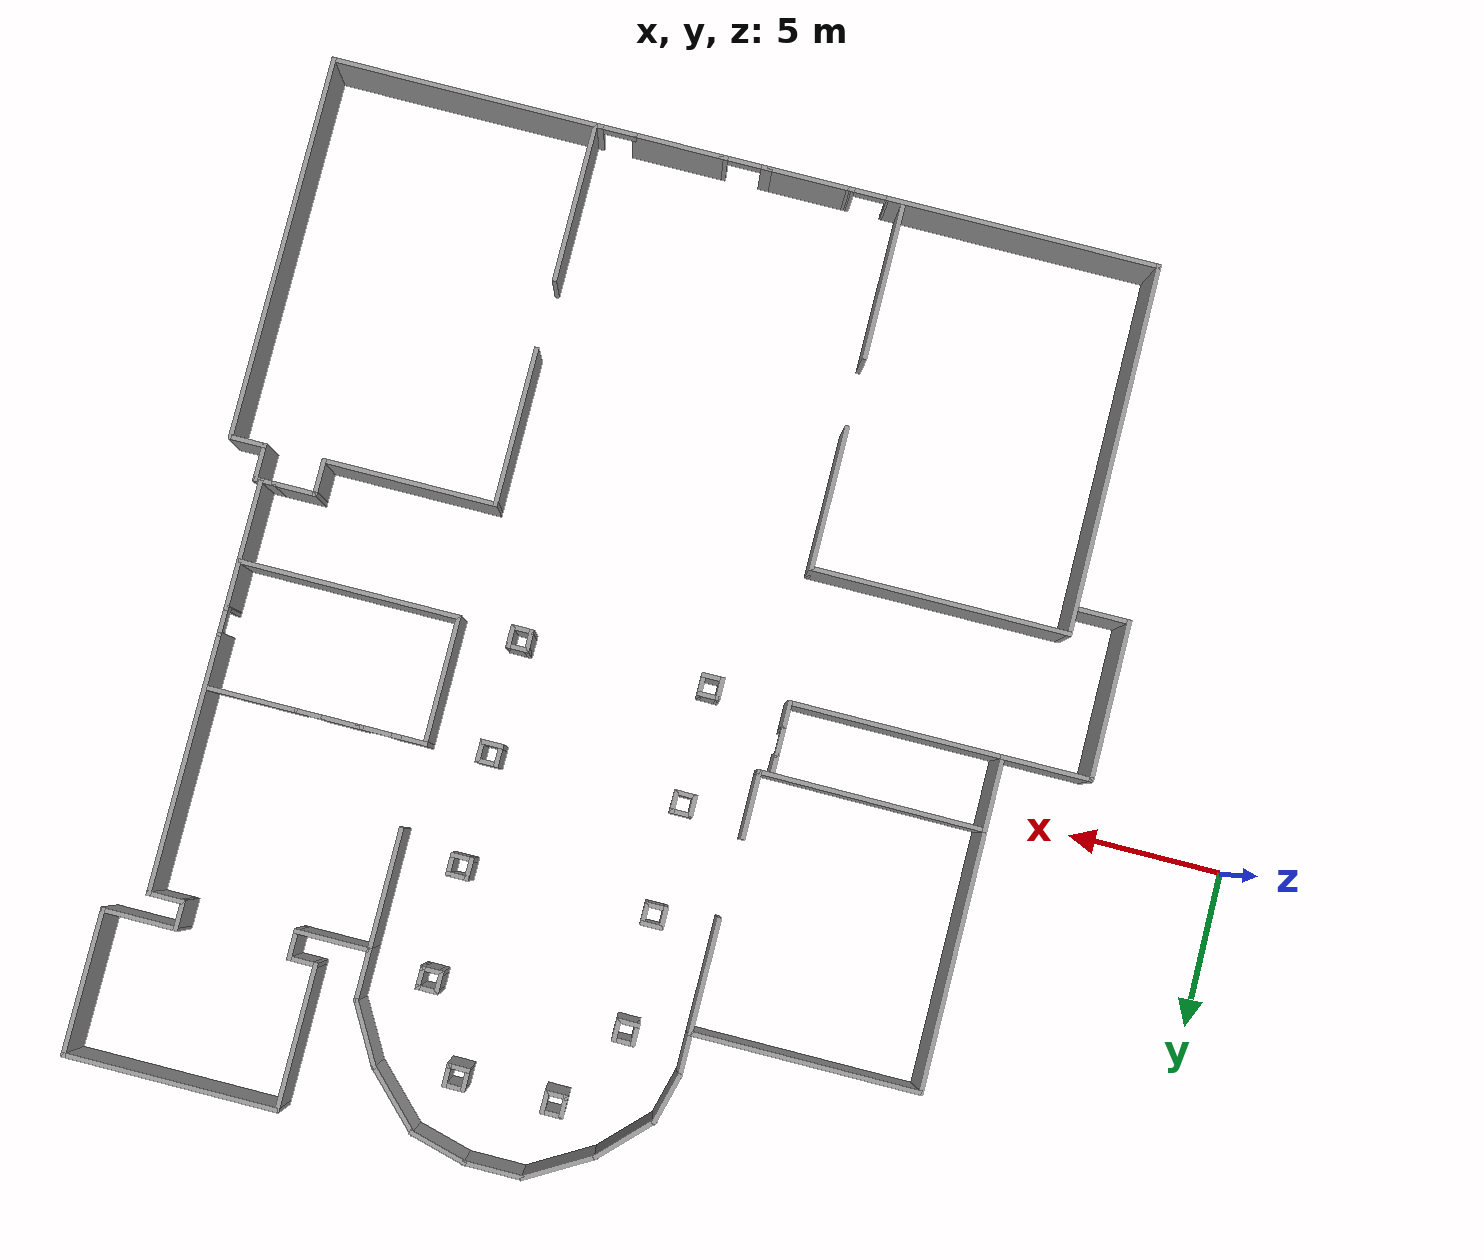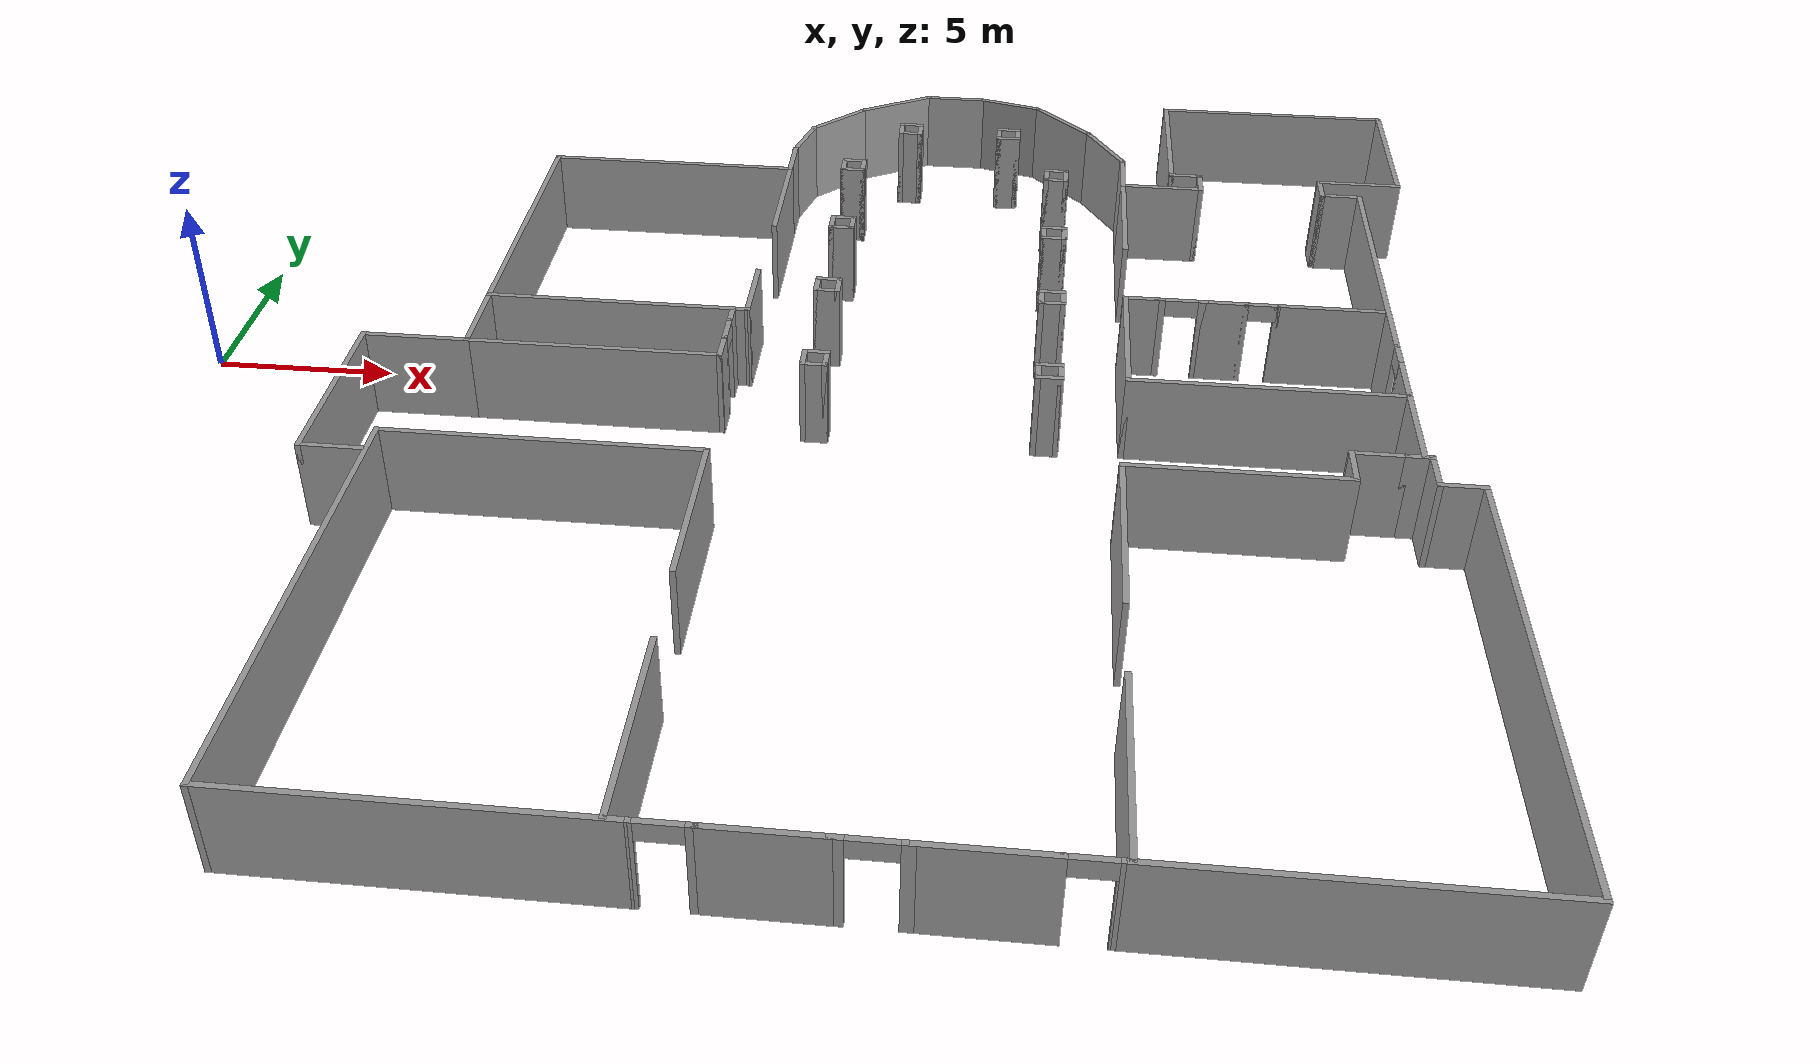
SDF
<?xml version='1.0'?>
<sdf version='1.6'>
  <model name='museum'>
    <pose frame=''>19.5611 -1.79807 0 0 -0 0</pose>
    <link name='Wall_0'>
      <collision name='Wall_0_Collision'>
        <geometry>
          <box>
            <size>7.5 0.15 2.5</size>
          </box>
        </geometry>
        <pose frame=''>0 0 1.25 0 -0 0</pose>
      </collision>
      <visual name='Wall_0_Visual'>
        <pose frame=''>0 0 1.25 0 -0 0</pose>
        <geometry>
          <box>
            <size>7.5 0.15 2.5</size>
          </box>
        </geometry>
        <material>
          <script>
            <uri>file://media/materials/scripts/gazebo.material</uri>
            <name>Gazebo/Grey</name>
          </script>
          <ambient>1 1 1 1</ambient>
        </material>
      </visual>
      <pose frame=''>-7.91012 10.7458 0 0 -0 0</pose>
    </link>
    <link name='Wall_1'>
      <collision name='Wall_1_Collision'>
        <geometry>
          <box>
            <size>3.75 0.15 2.5</size>
          </box>
        </geometry>
        <pose frame=''>0 0 1.25 0 -0 0</pose>
      </collision>
      <visual name='Wall_1_Visual'>
        <pose frame=''>0 0 1.25 0 -0 0</pose>
        <geometry>
          <box>
            <size>3.75 0.15 2.5</size>
          </box>
        </geometry>
        <material>
          <script>
            <uri>file://media/materials/scripts/gazebo.material</uri>
            <name>Gazebo/Grey</name>
          </script>
          <ambient>1 1 1 1</ambient>
        </material>
      </visual>
      <pose frame=''>-4.23512 8.94576 0 0 0 -1.5708</pose>
    </link>
    <link name='Wall_10'>
      <collision name='Wall_10_Collision'>
        <geometry>
          <box>
            <size>1.5 0.15 2.5</size>
          </box>
        </geometry>
        <pose frame=''>0 0 1.25 0 -0 0</pose>
      </collision>
      <visual name='Wall_10_Visual'>
        <pose frame=''>0 0 1.25 0 -0 0</pose>
        <geometry>
          <box>
            <size>1.5 0.15 2.5</size>
          </box>
        </geometry>
        <material>
          <script>
            <uri>file://media/materials/scripts/gazebo.material</uri>
            <name>Gazebo/Grey</name>
          </script>
          <ambient>1 1 1 1</ambient>
        </material>
      </visual>
      <pose frame=''>-4.23512 11.4208 0 0 -0 1.5708</pose>
    </link>
    <link name='Wall_115'>
      <collision name='Wall_115_Collision'>
        <geometry>
          <box>
            <size>2.5 0.15 2.5</size>
          </box>
        </geometry>
        <pose frame=''>0 0 1.25 0 -0 0</pose>
      </collision>
      <visual name='Wall_115_Visual'>
        <pose frame=''>0 0 1.25 0 -0 0</pose>
        <geometry>
          <box>
            <size>2.5 0.15 2.5</size>
          </box>
        </geometry>
        <material>
          <script>
            <uri>file://media/materials/scripts/gazebo.material</uri>
            <name>Gazebo/Grey</name>
          </script>
          <ambient>1 1 1 1</ambient>
        </material>
      </visual>
      <pose frame=''>-11.5851 1.22076 0 0 0 -1.5708</pose>
    </link>
    <link name='Wall_122'>
      <collision name='Wall_122_Collision'>
        <geometry>
          <box>
            <size>7 0.15 2.5</size>
          </box>
        </geometry>
        <pose frame=''>0 0 1.25 0 -0 0</pose>
      </collision>
      <visual name='Wall_122_Visual'>
        <pose frame=''>0 0 1.25 0 -0 0</pose>
        <geometry>
          <box>
            <size>7 0.15 2.5</size>
          </box>
        </geometry>
        <material>
          <script>
            <uri>file://media/materials/scripts/gazebo.material</uri>
            <name>Gazebo/Grey</name>
          </script>
          <ambient>1 1 1 1</ambient>
        </material>
      </visual>
      <pose frame=''>-8.16012 0.045757 0 0 -0 0</pose>
    </link>
    <link name='Wall_125'>
      <collision name='Wall_125_Collision'>
        <geometry>
          <box>
            <size>1 0.15 2.5</size>
          </box>
        </geometry>
        <pose frame=''>0 0 1.25 0 -0 0</pose>
      </collision>
      <visual name='Wall_125_Visual'>
        <pose frame=''>0 0 1.25 0 -0 0</pose>
        <geometry>
          <box>
            <size>1 0.15 2.5</size>
          </box>
        </geometry>
        <material>
          <script>
            <uri>file://media/materials/scripts/gazebo.material</uri>
            <name>Gazebo/Grey</name>
          </script>
          <ambient>1 1 1 1</ambient>
        </material>
      </visual>
      <pose frame=''>-4.73512 0.470757 0 0 -0 1.5708</pose>
    </link>
    <link name='Wall_126'>
      <pose frame=''>-4.73512 1.32076 0 0 -0 1.5708</pose>
      <visual name='Wall_126_Visual_0'>
        <pose frame=''>-0.480087 0 1.25 0 -0 0</pose>
        <geometry>
          <box>
            <size>0.039827 0.15 2.5</size>
          </box>
        </geometry>
        <material>
          <script>
            <uri>file://media/materials/scripts/gazebo.material</uri>
            <name>Gazebo/Grey</name>
          </script>
          <ambient>1 1 1 1</ambient>
        </material>
      </visual>
      <collision name='Wall_126_Collision_0'>
        <geometry>
          <box>
            <size>0.039827 0.15 2.5</size>
          </box>
        </geometry>
        <pose frame=''>-0.480087 0 1.25 0 -0 0</pose>
      </collision>
      <visual name='Wall_126_Visual_1'>
        <pose frame=''>0.469913 0 1.25 0 -0 0</pose>
        <geometry>
          <box>
            <size>0.060173 0.15 2.5</size>
          </box>
        </geometry>
        <material>
          <script>
            <uri>file://media/materials/scripts/gazebo.material</uri>
            <name>Gazebo/Grey</name>
          </script>
          <ambient>1 1 1 1</ambient>
        </material>
      </visual>
      <collision name='Wall_126_Collision_1'>
        <geometry>
          <box>
            <size>0.060173 0.15 2.5</size>
          </box>
        </geometry>
        <pose frame=''>0.469913 0 1.25 0 -0 0</pose>
      </collision>
      <visual name='Wall_126_Visual_2'>
        <pose frame=''>-0.010173 0 2.25 0 -0 0</pose>
        <geometry>
          <box>
            <size>0.9 0.15 0.5</size>
          </box>
        </geometry>
        <material>
          <script>
            <uri>file://media/materials/scripts/gazebo.material</uri>
            <name>Gazebo/Grey</name>
          </script>
          <ambient>1 1 1 1</ambient>
        </material>
      </visual>
      <collision name='Wall_126_Collision_2'>
        <geometry>
          <box>
            <size>0.9 0.15 0.5</size>
          </box>
        </geometry>
        <pose frame=''>-0.010173 0 2.25 0 -0 0</pose>
      </collision>
    </link>
    <link name='Wall_127'>
      <collision name='Wall_127_Collision'>
        <geometry>
          <box>
            <size>0.75 0.15 2.5</size>
          </box>
        </geometry>
        <pose frame=''>0 0 1.25 0 -0 0</pose>
      </collision>
      <visual name='Wall_127_Visual'>
        <pose frame=''>0 0 1.25 0 -0 0</pose>
        <geometry>
          <box>
            <size>0.75 0.15 2.5</size>
          </box>
        </geometry>
        <material>
          <script>
            <uri>file://media/materials/scripts/gazebo.material</uri>
            <name>Gazebo/Grey</name>
          </script>
          <ambient>1 1 1 1</ambient>
        </material>
      </visual>
      <pose frame=''>-4.73512 2.04576 0 0 -0 1.5708</pose>
    </link>
    <link name='Wall_135'>
      <collision name='Wall_135_Collision'>
        <geometry>
          <box>
            <size>3 0.15 2.5</size>
          </box>
        </geometry>
        <pose frame=''>0 0 1.25 0 -0 0</pose>
      </collision>
      <visual name='Wall_135_Visual'>
        <pose frame=''>0 0 1.25 0 -0 0</pose>
        <geometry>
          <box>
            <size>3 0.15 2.5</size>
          </box>
        </geometry>
        <material>
          <script>
            <uri>file://media/materials/scripts/gazebo.material</uri>
            <name>Gazebo/Grey</name>
          </script>
          <ambient>1 1 1 1</ambient>
        </material>
      </visual>
      <pose frame=''>-13.0101 0.045757 0 0 -0 3.14159</pose>
    </link>
    <link name='Wall_139'>
      <collision name='Wall_139_Collision'>
        <geometry>
          <box>
            <size>5.25 0.15 2.5</size>
          </box>
        </geometry>
        <pose frame=''>0 0 1.25 0 -0 0</pose>
      </collision>
      <visual name='Wall_139_Visual'>
        <pose frame=''>0 0 1.25 0 -0 0</pose>
        <geometry>
          <box>
            <size>5.25 0.15 2.5</size>
          </box>
        </geometry>
        <material>
          <script>
            <uri>file://media/materials/scripts/gazebo.material</uri>
            <name>Gazebo/Grey</name>
          </script>
          <ambient>1 1 1 1</ambient>
        </material>
      </visual>
      <pose frame=''>-14.4351 -2.50424 0 0 0 -1.5708</pose>
    </link>
    <link name='Wall_141'>
      <collision name='Wall_141_Collision'>
        <geometry>
          <box>
            <size>1.75 0.15 2.5</size>
          </box>
        </geometry>
        <pose frame=''>0 0 1.25 0 -0 0</pose>
      </collision>
      <visual name='Wall_141_Visual'>
        <pose frame=''>0 0 1.25 0 -0 0</pose>
        <geometry>
          <box>
            <size>1.75 0.15 2.5</size>
          </box>
        </geometry>
        <material>
          <script>
            <uri>file://media/materials/scripts/gazebo.material</uri>
            <name>Gazebo/Grey</name>
          </script>
          <ambient>1 1 1 1</ambient>
        </material>
      </visual>
      <pose frame=''>-13.6351 -5.05424 0 0 -0 0</pose>
    </link>
    <link name='Wall_146'>
      <pose frame=''>13.1477 1.96699 0 0 0 -1.5708</pose>
      <visual name='Wall_146_Visual_0'>
        <pose frame=''>-0.441517 0 1.25 0 -0 0</pose>
        <geometry>
          <box>
            <size>0.116967 0.15 2.5</size>
          </box>
        </geometry>
        <material>
          <script>
            <uri>file://media/materials/scripts/gazebo.material</uri>
            <name>Gazebo/Grey</name>
          </script>
          <ambient>1 1 1 1</ambient>
        </material>
      </visual>
      <collision name='Wall_146_Collision_0'>
        <geometry>
          <box>
            <size>0.116967 0.15 2.5</size>
          </box>
        </geometry>
        <pose frame=''>-0.441517 0 1.25 0 -0 0</pose>
      </collision>
      <visual name='Wall_146_Visual_1'>
        <pose frame=''>0.488483 0 1.25 0 -0 0</pose>
        <geometry>
          <box>
            <size>0.023033 0.15 2.5</size>
          </box>
        </geometry>
        <material>
          <script>
            <uri>file://media/materials/scripts/gazebo.material</uri>
            <name>Gazebo/Grey</name>
          </script>
          <ambient>1 1 1 1</ambient>
        </material>
      </visual>
      <collision name='Wall_146_Collision_1'>
        <geometry>
          <box>
            <size>0.023033 0.15 2.5</size>
          </box>
        </geometry>
        <pose frame=''>0.488483 0 1.25 0 -0 0</pose>
      </collision>
      <visual name='Wall_146_Visual_2'>
        <pose frame=''>0.046967 0 2.25 0 -0 0</pose>
        <geometry>
          <box>
            <size>0.86 0.15 0.5</size>
          </box>
        </geometry>
        <material>
          <script>
            <uri>file://media/materials/scripts/gazebo.material</uri>
            <name>Gazebo/Grey</name>
          </script>
          <ambient>1 1 1 1</ambient>
        </material>
      </visual>
      <collision name='Wall_146_Collision_2'>
        <geometry>
          <box>
            <size>0.86 0.15 0.5</size>
          </box>
        </geometry>
        <pose frame=''>0.046967 0 2.25 0 -0 0</pose>
      </collision>
    </link>
    <link name='Wall_15'>
      <collision name='Wall_15_Collision'>
        <geometry>
          <box>
            <size>1.75 0.15 2.5</size>
          </box>
        </geometry>
        <pose frame=''>0 0 1.25 0 -0 0</pose>
      </collision>
      <visual name='Wall_15_Visual'>
        <pose frame=''>0 0 1.25 0 -0 0</pose>
        <geometry>
          <box>
            <size>1.75 0.15 2.5</size>
          </box>
        </geometry>
        <material>
          <script>
            <uri>file://media/materials/scripts/gazebo.material</uri>
            <name>Gazebo/Grey</name>
          </script>
          <ambient>1 1 1 1</ambient>
        </material>
      </visual>
      <pose frame=''>-4.02806 12.8685 0 0 -0 1.309</pose>
    </link>
    <link name='Wall_16'>
      <collision name='Wall_16_Collision'>
        <geometry>
          <box>
            <size>2.25 0.15 2.5</size>
          </box>
        </geometry>
        <pose frame=''>0 0 1.25 0 -0 0</pose>
      </collision>
      <visual name='Wall_16_Visual'>
        <pose frame=''>0 0 1.25 0 -0 0</pose>
        <geometry>
          <box>
            <size>2.25 0.15 2.5</size>
          </box>
        </geometry>
        <material>
          <script>
            <uri>file://media/materials/scripts/gazebo.material</uri>
            <name>Gazebo/Grey</name>
          </script>
          <ambient>1 1 1 1</ambient>
        </material>
      </visual>
      <pose frame=''>-3.07855 14.3837 0 0 -0 0.785398</pose>
    </link>
    <link name='Wall_160'>
      <collision name='Wall_160_Collision'>
        <geometry>
          <box>
            <size>4.25 0.15 2.5</size>
          </box>
        </geometry>
        <pose frame=''>0 0 1.25 0 -0 0</pose>
      </collision>
      <visual name='Wall_160_Visual'>
        <pose frame=''>0 0 1.25 0 -0 0</pose>
        <geometry>
          <box>
            <size>4.25 0.15 2.5</size>
          </box>
        </geometry>
        <material>
          <script>
            <uri>file://media/materials/scripts/gazebo.material</uri>
            <name>Gazebo/Grey</name>
          </script>
          <ambient>1 1 1 1</ambient>
        </material>
      </visual>
      <pose frame=''>13.1477 -0.508007 0 0 0 -1.5708</pose>
    </link>
    <link name='Wall_166'>
      <collision name='Wall_166_Collision'>
        <geometry>
          <box>
            <size>5.25 0.15 2.5</size>
          </box>
        </geometry>
        <pose frame=''>0 0 1.25 0 -0 0</pose>
      </collision>
      <visual name='Wall_166_Visual'>
        <pose frame=''>0 0 1.25 0 -0 0</pose>
        <geometry>
          <box>
            <size>5.25 0.15 2.5</size>
          </box>
        </geometry>
        <material>
          <script>
            <uri>file://media/materials/scripts/gazebo.material</uri>
            <name>Gazebo/Grey</name>
          </script>
          <ambient>1 1 1 1</ambient>
        </material>
      </visual>
      <pose frame=''>-4.36045 -13.7284 0 0 0 -1.5708</pose>
    </link>
    <link name='Wall_17'>
      <collision name='Wall_17_Collision'>
        <geometry>
          <box>
            <size>2.5 0.15 2.5</size>
          </box>
        </geometry>
        <pose frame=''>0 0 1.25 0 -0 0</pose>
      </collision>
      <visual name='Wall_17_Visual'>
        <pose frame=''>0 0 1.25 0 -0 0</pose>
        <geometry>
          <box>
            <size>2.5 0.15 2.5</size>
          </box>
        </geometry>
        <material>
          <script>
            <uri>file://media/materials/scripts/gazebo.material</uri>
            <name>Gazebo/Grey</name>
          </script>
          <ambient>1 1 1 1</ambient>
        </material>
      </visual>
      <pose frame=''>-1.3185 15.7137 0 0 -0 0.523599</pose>
    </link>
    <link name='Wall_170'>
      <collision name='Wall_170_Collision'>
        <geometry>
          <box>
            <size>3 0.15 2.5</size>
          </box>
        </geometry>
        <pose frame=''>0 0 1.25 0 -0 0</pose>
      </collision>
      <visual name='Wall_170_Visual'>
        <pose frame=''>0 0 1.25 0 -0 0</pose>
        <geometry>
          <box>
            <size>3 0.15 2.5</size>
          </box>
        </geometry>
        <material>
          <script>
            <uri>file://media/materials/scripts/gazebo.material</uri>
            <name>Gazebo/Grey</name>
          </script>
          <ambient>1 1 1 1</ambient>
        </material>
      </visual>
      <pose frame=''>3.06012 -16.3249 0 0 -0 3.14159</pose>
    </link>
    <link name='Wall_18'>
      <collision name='Wall_18_Collision'>
        <geometry>
          <box>
            <size>2 0.15 2.5</size>
          </box>
        </geometry>
        <pose frame=''>0 0 1.25 0 -0 0</pose>
      </collision>
      <visual name='Wall_18_Visual'>
        <pose frame=''>0 0 1.25 0 -0 0</pose>
        <geometry>
          <box>
            <size>2 0.15 2.5</size>
          </box>
        </geometry>
        <material>
          <script>
            <uri>file://media/materials/scripts/gazebo.material</uri>
            <name>Gazebo/Grey</name>
          </script>
          <ambient>1 1 1 1</ambient>
        </material>
      </visual>
      <pose frame=''>0.624076 16.3012 0 0 -0 0</pose>
    </link>
    <link name='Wall_184'>
      <pose frame=''>7.52862 4.1183 0 0 -0 0</pose>
      <visual name='Wall_184_Visual_0'>
        <pose frame=''>-0.586918 0 1.25 0 -0 0</pose>
        <geometry>
          <box>
            <size>0.326163 0.15 2.5</size>
          </box>
        </geometry>
        <material>
          <script>
            <uri>file://media/materials/scripts/gazebo.material</uri>
            <name>Gazebo/Grey</name>
          </script>
          <ambient>1 1 1 1</ambient>
        </material>
      </visual>
      <collision name='Wall_184_Collision_0'>
        <geometry>
          <box>
            <size>0.326163 0.15 2.5</size>
          </box>
        </geometry>
        <pose frame=''>-0.586918 0 1.25 0 -0 0</pose>
      </collision>
      <visual name='Wall_184_Visual_1'>
        <pose frame=''>0.613082 0 1.25 0 -0 0</pose>
        <geometry>
          <box>
            <size>0.273837 0.15 2.5</size>
          </box>
        </geometry>
        <material>
          <script>
            <uri>file://media/materials/scripts/gazebo.material</uri>
            <name>Gazebo/Grey</name>
          </script>
          <ambient>1 1 1 1</ambient>
        </material>
      </visual>
      <collision name='Wall_184_Collision_1'>
        <geometry>
          <box>
            <size>0.273837 0.15 2.5</size>
          </box>
        </geometry>
        <pose frame=''>0.613082 0 1.25 0 -0 0</pose>
      </collision>
      <visual name='Wall_184_Visual_2'>
        <pose frame=''>0.026163 0 2.25 0 -0 0</pose>
        <geometry>
          <box>
            <size>0.9 0.15 0.5</size>
          </box>
        </geometry>
        <material>
          <script>
            <uri>file://media/materials/scripts/gazebo.material</uri>
            <name>Gazebo/Grey</name>
          </script>
          <ambient>1 1 1 1</ambient>
        </material>
      </visual>
      <collision name='Wall_184_Collision_2'>
        <geometry>
          <box>
            <size>0.9 0.15 0.5</size>
          </box>
        </geometry>
        <pose frame=''>0.026163 0 2.25 0 -0 0</pose>
      </collision>
    </link>
    <link name='Wall_185'>
      <collision name='Wall_185_Collision'>
        <geometry>
          <box>
            <size>1.25 0.15 2.5</size>
          </box>
        </geometry>
        <pose frame=''>0 0 1.25 0 -0 0</pose>
      </collision>
      <visual name='Wall_185_Visual'>
        <pose frame=''>0 0 1.25 0 -0 0</pose>
        <geometry>
          <box>
            <size>1.25 0.15 2.5</size>
          </box>
        </geometry>
        <material>
          <script>
            <uri>file://media/materials/scripts/gazebo.material</uri>
            <name>Gazebo/Grey</name>
          </script>
          <ambient>1 1 1 1</ambient>
        </material>
      </visual>
      <pose frame=''>8.75362 4.1183 0 0 -0 0</pose>
    </link>
    <link name='Wall_186'>
      <pose frame=''>9.72862 4.1183 0 0 -0 0</pose>
      <visual name='Wall_186_Visual_0'>
        <pose frame=''>-0.486669 0 1.25 0 -0 0</pose>
        <geometry>
          <box>
            <size>0.026662 0.15 2.5</size>
          </box>
        </geometry>
        <material>
          <script>
            <uri>file://media/materials/scripts/gazebo.material</uri>
            <name>Gazebo/Grey</name>
          </script>
          <ambient>1 1 1 1</ambient>
        </material>
      </visual>
      <collision name='Wall_186_Collision_0'>
        <geometry>
          <box>
            <size>0.026662 0.15 2.5</size>
          </box>
        </geometry>
        <pose frame=''>-0.486669 0 1.25 0 -0 0</pose>
      </collision>
      <visual name='Wall_186_Visual_1'>
        <pose frame=''>0.463331 0 1.25 0 -0 0</pose>
        <geometry>
          <box>
            <size>0.073338 0.15 2.5</size>
          </box>
        </geometry>
        <material>
          <script>
            <uri>file://media/materials/scripts/gazebo.material</uri>
            <name>Gazebo/Grey</name>
          </script>
          <ambient>1 1 1 1</ambient>
        </material>
      </visual>
      <collision name='Wall_186_Collision_1'>
        <geometry>
          <box>
            <size>0.073338 0.15 2.5</size>
          </box>
        </geometry>
        <pose frame=''>0.463331 0 1.25 0 -0 0</pose>
      </collision>
      <visual name='Wall_186_Visual_2'>
        <pose frame=''>-0.023338 0 2.25 0 -0 0</pose>
        <geometry>
          <box>
            <size>0.9 0.15 0.5</size>
          </box>
        </geometry>
        <material>
          <script>
            <uri>file://media/materials/scripts/gazebo.material</uri>
            <name>Gazebo/Grey</name>
          </script>
          <ambient>1 1 1 1</ambient>
        </material>
      </visual>
      <collision name='Wall_186_Collision_2'>
        <geometry>
          <box>
            <size>0.9 0.15 0.5</size>
          </box>
        </geometry>
        <pose frame=''>-0.023338 0 2.25 0 -0 0</pose>
      </collision>
    </link>
    <link name='Wall_187'>
      <collision name='Wall_187_Collision'>
        <geometry>
          <box>
            <size>3 0.15 2.5</size>
          </box>
        </geometry>
        <pose frame=''>0 0 1.25 0 -0 0</pose>
      </collision>
      <visual name='Wall_187_Visual'>
        <pose frame=''>0 0 1.25 0 -0 0</pose>
        <geometry>
          <box>
            <size>3 0.15 2.5</size>
          </box>
        </geometry>
        <material>
          <script>
            <uri>file://media/materials/scripts/gazebo.material</uri>
            <name>Gazebo/Grey</name>
          </script>
          <ambient>1 1 1 1</ambient>
        </material>
      </visual>
      <pose frame=''>11.5786 4.1183 0 0 -0 0</pose>
    </link>
    <link name='Wall_189'>
      <collision name='Wall_189_Collision'>
        <geometry>
          <box>
            <size>4 0.15 2.5</size>
          </box>
        </geometry>
        <pose frame=''>0 0 1.25 0 -0 0</pose>
      </collision>
      <visual name='Wall_189_Visual'>
        <pose frame=''>0 0 1.25 0 -0 0</pose>
        <geometry>
          <box>
            <size>4 0.15 2.5</size>
          </box>
        </geometry>
        <material>
          <script>
            <uri>file://media/materials/scripts/gazebo.material</uri>
            <name>Gazebo/Grey</name>
          </script>
          <ambient>1 1 1 1</ambient>
        </material>
      </visual>
      <pose frame=''>6.04774 8.81699 0 0 0 -1.5708</pose>
    </link>
    <link name='Wall_19'>
      <collision name='Wall_19_Collision'>
        <geometry>
          <box>
            <size>2 0.15 2.5</size>
          </box>
        </geometry>
        <pose frame=''>0 0 1.25 0 -0 0</pose>
      </collision>
      <visual name='Wall_19_Visual'>
        <pose frame=''>0 0 1.25 0 -0 0</pose>
        <geometry>
          <box>
            <size>2 0.15 2.5</size>
          </box>
        </geometry>
        <material>
          <script>
            <uri>file://media/materials/scripts/gazebo.material</uri>
            <name>Gazebo/Grey</name>
          </script>
          <ambient>1 1 1 1</ambient>
        </material>
      </visual>
      <pose frame=''>2.44256 16.0618 0 0 0 -0.261799</pose>
    </link>
    <link name='Wall_192'>
      <collision name='Wall_192_Collision'>
        <geometry>
          <box>
            <size>0.75 0.15 2.5</size>
          </box>
        </geometry>
        <pose frame=''>0 0 1.25 0 -0 0</pose>
      </collision>
      <visual name='Wall_192_Visual'>
        <pose frame=''>0 0 1.25 0 -0 0</pose>
        <geometry>
          <box>
            <size>0.75 0.15 2.5</size>
          </box>
        </geometry>
        <material>
          <script>
            <uri>file://media/materials/scripts/gazebo.material</uri>
            <name>Gazebo/Grey</name>
          </script>
          <ambient>1 1 1 1</ambient>
        </material>
      </visual>
      <pose frame=''>-2.20621 0.469078 0 0 -0 0</pose>
    </link>
    <link name='Wall_193'>
      <collision name='Wall_193_Collision'>
        <geometry>
          <box>
            <size>0.75 0.15 2.5</size>
          </box>
        </geometry>
        <pose frame=''>0 0 1.25 0 -0 0</pose>
      </collision>
      <visual name='Wall_193_Visual'>
        <pose frame=''>0 0 1.25 0 -0 0</pose>
        <geometry>
          <box>
            <size>0.75 0.15 2.5</size>
          </box>
        </geometry>
        <material>
          <script>
            <uri>file://media/materials/scripts/gazebo.material</uri>
            <name>Gazebo/Grey</name>
          </script>
          <ambient>1 1 1 1</ambient>
        </material>
      </visual>
      <pose frame=''>-1.90621 0.169078 0 0 0 -1.5708</pose>
    </link>
    <link name='Wall_194'>
      <collision name='Wall_194_Collision'>
        <geometry>
          <box>
            <size>0.75 0.15 2.5</size>
          </box>
        </geometry>
        <pose frame=''>0 0 1.25 0 -0 0</pose>
      </collision>
      <visual name='Wall_194_Visual'>
        <pose frame=''>0 0 1.25 0 -0 0</pose>
        <geometry>
          <box>
            <size>0.75 0.15 2.5</size>
          </box>
        </geometry>
        <material>
          <script>
            <uri>file://media/materials/scripts/gazebo.material</uri>
            <name>Gazebo/Grey</name>
          </script>
          <ambient>1 1 1 1</ambient>
        </material>
      </visual>
      <pose frame=''>-2.20621 -0.130922 0 0 -0 3.14159</pose>
    </link>
    <link name='Wall_195'>
      <collision name='Wall_195_Collision'>
        <geometry>
          <box>
            <size>0.75 0.15 2.5</size>
          </box>
        </geometry>
        <pose frame=''>0 0 1.25 0 -0 0</pose>
      </collision>
      <visual name='Wall_195_Visual'>
        <pose frame=''>0 0 1.25 0 -0 0</pose>
        <geometry>
          <box>
            <size>0.75 0.15 2.5</size>
          </box>
        </geometry>
        <material>
          <script>
            <uri>file://media/materials/scripts/gazebo.material</uri>
            <name>Gazebo/Grey</name>
          </script>
          <ambient>1 1 1 1</ambient>
        </material>
      </visual>
      <pose frame=''>-2.50622 0.169078 0 0 -0 1.5708</pose>
    </link>
    <link name='Wall_197'>
      <collision name='Wall_197_Collision'>
        <geometry>
          <box>
            <size>0.75 0.15 2.5</size>
          </box>
        </geometry>
        <pose frame=''>0 0 1.25 0 -0 0</pose>
      </collision>
      <visual name='Wall_197_Visual'>
        <pose frame=''>0 0 1.25 0 -0 0</pose>
        <geometry>
          <box>
            <size>0.75 0.15 2.5</size>
          </box>
        </geometry>
        <material>
          <script>
            <uri>file://media/materials/scripts/gazebo.material</uri>
            <name>Gazebo/Grey</name>
          </script>
          <ambient>1 1 1 1</ambient>
        </material>
      </visual>
      <pose frame=''>3.9677 0.495165 0 0 -0 0</pose>
    </link>
    <link name='Wall_198'>
      <collision name='Wall_198_Collision'>
        <geometry>
          <box>
            <size>0.75 0.15 2.5</size>
          </box>
        </geometry>
        <pose frame=''>0 0 1.25 0 -0 0</pose>
      </collision>
      <visual name='Wall_198_Visual'>
        <pose frame=''>0 0 1.25 0 -0 0</pose>
        <geometry>
          <box>
            <size>0.75 0.15 2.5</size>
          </box>
        </geometry>
        <material>
          <script>
            <uri>file://media/materials/scripts/gazebo.material</uri>
            <name>Gazebo/Grey</name>
          </script>
          <ambient>1 1 1 1</ambient>
        </material>
      </visual>
      <pose frame=''>4.2677 0.195165 0 0 0 -1.5708</pose>
    </link>
    <link name='Wall_199'>
      <collision name='Wall_199_Collision'>
        <geometry>
          <box>
            <size>0.75 0.15 2.5</size>
          </box>
        </geometry>
        <pose frame=''>0 0 1.25 0 -0 0</pose>
      </collision>
      <visual name='Wall_199_Visual'>
        <pose frame=''>0 0 1.25 0 -0 0</pose>
        <geometry>
          <box>
            <size>0.75 0.15 2.5</size>
          </box>
        </geometry>
        <material>
          <script>
            <uri>file://media/materials/scripts/gazebo.material</uri>
            <name>Gazebo/Grey</name>
          </script>
          <ambient>1 1 1 1</ambient>
        </material>
      </visual>
      <pose frame=''>3.9677 -0.104835 0 0 -0 3.14159</pose>
    </link>
    <link name='Wall_20'>
      <collision name='Wall_20_Collision'>
        <geometry>
          <box>
            <size>2.5 0.15 2.5</size>
          </box>
        </geometry>
        <pose frame=''>0 0 1.25 0 -0 0</pose>
      </collision>
      <visual name='Wall_20_Visual'>
        <pose frame=''>0 0 1.25 0 -0 0</pose>
        <geometry>
          <box>
            <size>2.5 0.15 2.5</size>
          </box>
        </geometry>
        <material>
          <script>
            <uri>file://media/materials/scripts/gazebo.material</uri>
            <name>Gazebo/Grey</name>
          </script>
          <ambient>1 1 1 1</ambient>
        </material>
      </visual>
      <pose frame=''>4.16689 14.9915 0 0 0 -0.785398</pose>
    </link>
    <link name='Wall_200'>
      <collision name='Wall_200_Collision'>
        <geometry>
          <box>
            <size>0.75 0.15 2.5</size>
          </box>
        </geometry>
        <pose frame=''>0 0 1.25 0 -0 0</pose>
      </collision>
      <visual name='Wall_200_Visual'>
        <pose frame=''>0 0 1.25 0 -0 0</pose>
        <geometry>
          <box>
            <size>0.75 0.15 2.5</size>
          </box>
        </geometry>
        <material>
          <script>
            <uri>file://media/materials/scripts/gazebo.material</uri>
            <name>Gazebo/Grey</name>
          </script>
          <ambient>1 1 1 1</ambient>
        </material>
      </visual>
      <pose frame=''>3.6677 0.195165 0 0 -0 1.5708</pose>
    </link>
    <link name='Wall_202'>
      <collision name='Wall_202_Collision'>
        <geometry>
          <box>
            <size>0.75 0.15 2.5</size>
          </box>
        </geometry>
        <pose frame=''>0 0 1.25 0 -0 0</pose>
      </collision>
      <visual name='Wall_202_Visual'>
        <pose frame=''>0 0 1.25 0 -0 0</pose>
        <geometry>
          <box>
            <size>0.75 0.15 2.5</size>
          </box>
        </geometry>
        <material>
          <script>
            <uri>file://media/materials/scripts/gazebo.material</uri>
            <name>Gazebo/Grey</name>
          </script>
          <ambient>1 1 1 1</ambient>
        </material>
      </visual>
      <pose frame=''>-2.28448 4.2343 0 0 -0 0</pose>
    </link>
    <link name='Wall_203'>
      <collision name='Wall_203_Collision'>
        <geometry>
          <box>
            <size>0.75 0.15 2.5</size>
          </box>
        </geometry>
        <pose frame=''>0 0 1.25 0 -0 0</pose>
      </collision>
      <visual name='Wall_203_Visual'>
        <pose frame=''>0 0 1.25 0 -0 0</pose>
        <geometry>
          <box>
            <size>0.75 0.15 2.5</size>
          </box>
        </geometry>
        <material>
          <script>
            <uri>file://media/materials/scripts/gazebo.material</uri>
            <name>Gazebo/Grey</name>
          </script>
          <ambient>1 1 1 1</ambient>
        </material>
      </visual>
      <pose frame=''>-1.98447 3.9343 0 0 0 -1.5708</pose>
    </link>
    <link name='Wall_204'>
      <collision name='Wall_204_Collision'>
        <geometry>
          <box>
            <size>0.75 0.15 2.5</size>
          </box>
        </geometry>
        <pose frame=''>0 0 1.25 0 -0 0</pose>
      </collision>
      <visual name='Wall_204_Visual'>
        <pose frame=''>0 0 1.25 0 -0 0</pose>
        <geometry>
          <box>
            <size>0.75 0.15 2.5</size>
          </box>
        </geometry>
        <material>
          <script>
            <uri>file://media/materials/scripts/gazebo.material</uri>
            <name>Gazebo/Grey</name>
          </script>
          <ambient>1 1 1 1</ambient>
        </material>
      </visual>
      <pose frame=''>-2.28448 3.6343 0 0 -0 3.14159</pose>
    </link>
    <link name='Wall_205'>
      <collision name='Wall_205_Collision'>
        <geometry>
          <box>
            <size>0.75 0.15 2.5</size>
          </box>
        </geometry>
        <pose frame=''>0 0 1.25 0 -0 0</pose>
      </collision>
      <visual name='Wall_205_Visual'>
        <pose frame=''>0 0 1.25 0 -0 0</pose>
        <geometry>
          <box>
            <size>0.75 0.15 2.5</size>
          </box>
        </geometry>
        <material>
          <script>
            <uri>file://media/materials/scripts/gazebo.material</uri>
            <name>Gazebo/Grey</name>
          </script>
          <ambient>1 1 1 1</ambient>
        </material>
      </visual>
      <pose frame=''>-2.58448 3.9343 0 0 -0 1.5708</pose>
    </link>
    <link name='Wall_207'>
      <collision name='Wall_207_Collision'>
        <geometry>
          <box>
            <size>0.75 0.15 2.5</size>
          </box>
        </geometry>
        <pose frame=''>0 0 1.25 0 -0 0</pose>
      </collision>
      <visual name='Wall_207_Visual'>
        <pose frame=''>0 0 1.25 0 -0 0</pose>
        <geometry>
          <box>
            <size>0.75 0.15 2.5</size>
          </box>
        </geometry>
        <material>
          <script>
            <uri>file://media/materials/scripts/gazebo.material</uri>
            <name>Gazebo/Grey</name>
          </script>
          <ambient>1 1 1 1</ambient>
        </material>
      </visual>
      <pose frame=''>3.98509 4.20821 0 0 -0 0</pose>
    </link>
    <link name='Wall_208'>
      <collision name='Wall_208_Collision'>
        <geometry>
          <box>
            <size>0.75 0.15 2.5</size>
          </box>
        </geometry>
        <pose frame=''>0 0 1.25 0 -0 0</pose>
      </collision>
      <visual name='Wall_208_Visual'>
        <pose frame=''>0 0 1.25 0 -0 0</pose>
        <geometry>
          <box>
            <size>0.75 0.15 2.5</size>
          </box>
        </geometry>
        <material>
          <script>
            <uri>file://media/materials/scripts/gazebo.material</uri>
            <name>Gazebo/Grey</name>
          </script>
          <ambient>1 1 1 1</ambient>
        </material>
      </visual>
      <pose frame=''>4.28509 3.90821 0 0 0 -1.5708</pose>
    </link>
    <link name='Wall_209'>
      <collision name='Wall_209_Collision'>
        <geometry>
          <box>
            <size>0.75 0.15 2.5</size>
          </box>
        </geometry>
        <pose frame=''>0 0 1.25 0 -0 0</pose>
      </collision>
      <visual name='Wall_209_Visual'>
        <pose frame=''>0 0 1.25 0 -0 0</pose>
        <geometry>
          <box>
            <size>0.75 0.15 2.5</size>
          </box>
        </geometry>
        <material>
          <script>
            <uri>file://media/materials/scripts/gazebo.material</uri>
            <name>Gazebo/Grey</name>
          </script>
          <ambient>1 1 1 1</ambient>
        </material>
      </visual>
      <pose frame=''>3.98509 3.60821 0 0 -0 3.14159</pose>
    </link>
    <link name='Wall_21'>
      <collision name='Wall_21_Collision'>
        <geometry>
          <box>
            <size>2.25 0.15 2.5</size>
          </box>
        </geometry>
        <pose frame=''>0 0 1.25 0 -0 0</pose>
      </collision>
      <visual name='Wall_21_Visual'>
        <pose frame=''>0 0 1.25 0 -0 0</pose>
        <geometry>
          <box>
            <size>2.25 0.15 2.5</size>
          </box>
        </geometry>
        <material>
          <script>
            <uri>file://media/materials/scripts/gazebo.material</uri>
            <name>Gazebo/Grey</name>
          </script>
          <ambient>1 1 1 1</ambient>
        </material>
      </visual>
      <pose frame=''>5.52274 13.2513 0 0 0 -1.0472</pose>
    </link>
    <link name='Wall_210'>
      <collision name='Wall_210_Collision'>
        <geometry>
          <box>
            <size>0.75 0.15 2.5</size>
          </box>
        </geometry>
        <pose frame=''>0 0 1.25 0 -0 0</pose>
      </collision>
      <visual name='Wall_210_Visual'>
        <pose frame=''>0 0 1.25 0 -0 0</pose>
        <geometry>
          <box>
            <size>0.75 0.15 2.5</size>
          </box>
        </geometry>
        <material>
          <script>
            <uri>file://media/materials/scripts/gazebo.material</uri>
            <name>Gazebo/Grey</name>
          </script>
          <ambient>1 1 1 1</ambient>
        </material>
      </visual>
      <pose frame=''>3.68509 3.90821 0 0 -0 1.5708</pose>
    </link>
    <link name='Wall_212'>
      <collision name='Wall_212_Collision'>
        <geometry>
          <box>
            <size>0.75 0.15 2.5</size>
          </box>
        </geometry>
        <pose frame=''>0 0 1.25 0 -0 0</pose>
      </collision>
      <visual name='Wall_212_Visual'>
        <pose frame=''>0 0 1.25 0 -0 0</pose>
        <geometry>
          <box>
            <size>0.75 0.15 2.5</size>
          </box>
        </geometry>
        <material>
          <script>
            <uri>file://media/materials/scripts/gazebo.material</uri>
            <name>Gazebo/Grey</name>
          </script>
          <ambient>1 1 1 1</ambient>
        </material>
      </visual>
      <pose frame=''>-2.25839 7.8256 0 0 -0 0</pose>
    </link>
    <link name='Wall_213'>
      <collision name='Wall_213_Collision'>
        <geometry>
          <box>
            <size>0.75 0.15 2.5</size>
          </box>
        </geometry>
        <pose frame=''>0 0 1.25 0 -0 0</pose>
      </collision>
      <visual name='Wall_213_Visual'>
        <pose frame=''>0 0 1.25 0 -0 0</pose>
        <geometry>
          <box>
            <size>0.75 0.15 2.5</size>
          </box>
        </geometry>
        <material>
          <script>
            <uri>file://media/materials/scripts/gazebo.material</uri>
            <name>Gazebo/Grey</name>
          </script>
          <ambient>1 1 1 1</ambient>
        </material>
      </visual>
      <pose frame=''>-1.95839 7.5256 0 0 0 -1.5708</pose>
    </link>
    <link name='Wall_214'>
      <collision name='Wall_214_Collision'>
        <geometry>
          <box>
            <size>0.75 0.15 2.5</size>
          </box>
        </geometry>
        <pose frame=''>0 0 1.25 0 -0 0</pose>
      </collision>
      <visual name='Wall_214_Visual'>
        <pose frame=''>0 0 1.25 0 -0 0</pose>
        <geometry>
          <box>
            <size>0.75 0.15 2.5</size>
          </box>
        </geometry>
        <material>
          <script>
            <uri>file://media/materials/scripts/gazebo.material</uri>
            <name>Gazebo/Grey</name>
          </script>
          <ambient>1 1 1 1</ambient>
        </material>
      </visual>
      <pose frame=''>-2.25839 7.2256 0 0 -0 3.14159</pose>
    </link>
    <link name='Wall_215'>
      <collision name='Wall_215_Collision'>
        <geometry>
          <box>
            <size>0.75 0.15 2.5</size>
          </box>
        </geometry>
        <pose frame=''>0 0 1.25 0 -0 0</pose>
      </collision>
      <visual name='Wall_215_Visual'>
        <pose frame=''>0 0 1.25 0 -0 0</pose>
        <geometry>
          <box>
            <size>0.75 0.15 2.5</size>
          </box>
        </geometry>
        <material>
          <script>
            <uri>file://media/materials/scripts/gazebo.material</uri>
            <name>Gazebo/Grey</name>
          </script>
          <ambient>1 1 1 1</ambient>
        </material>
      </visual>
      <pose frame=''>-2.55839 7.5256 0 0 -0 1.5708</pose>
    </link>
    <link name='Wall_217'>
      <collision name='Wall_217_Collision'>
        <geometry>
          <box>
            <size>0.75 0.15 2.5</size>
          </box>
        </geometry>
        <pose frame=''>0 0 1.25 0 -0 0</pose>
      </collision>
      <visual name='Wall_217_Visual'>
        <pose frame=''>0 0 1.25 0 -0 0</pose>
        <geometry>
          <box>
            <size>0.75 0.15 2.5</size>
          </box>
        </geometry>
        <material>
          <script>
            <uri>file://media/materials/scripts/gazebo.material</uri>
            <name>Gazebo/Grey</name>
          </script>
          <ambient>1 1 1 1</ambient>
        </material>
      </visual>
      <pose frame=''>3.98509 7.85169 0 0 -0 0</pose>
    </link>
    <link name='Wall_218'>
      <collision name='Wall_218_Collision'>
        <geometry>
          <box>
            <size>0.75 0.15 2.5</size>
          </box>
        </geometry>
        <pose frame=''>0 0 1.25 0 -0 0</pose>
      </collision>
      <visual name='Wall_218_Visual'>
        <pose frame=''>0 0 1.25 0 -0 0</pose>
        <geometry>
          <box>
            <size>0.75 0.15 2.5</size>
          </box>
        </geometry>
        <material>
          <script>
            <uri>file://media/materials/scripts/gazebo.material</uri>
            <name>Gazebo/Grey</name>
          </script>
          <ambient>1 1 1 1</ambient>
        </material>
      </visual>
      <pose frame=''>4.28509 7.55169 0 0 0 -1.5708</pose>
    </link>
    <link name='Wall_219'>
      <collision name='Wall_219_Collision'>
        <geometry>
          <box>
            <size>0.75 0.15 2.5</size>
          </box>
        </geometry>
        <pose frame=''>0 0 1.25 0 -0 0</pose>
      </collision>
      <visual name='Wall_219_Visual'>
        <pose frame=''>0 0 1.25 0 -0 0</pose>
        <geometry>
          <box>
            <size>0.75 0.15 2.5</size>
          </box>
        </geometry>
        <material>
          <script>
            <uri>file://media/materials/scripts/gazebo.material</uri>
            <name>Gazebo/Grey</name>
          </script>
          <ambient>1 1 1 1</ambient>
        </material>
      </visual>
      <pose frame=''>3.98509 7.25169 0 0 -0 3.14159</pose>
    </link>
    <link name='Wall_22'>
      <collision name='Wall_22_Collision'>
        <geometry>
          <box>
            <size>1.75 0.15 2.5</size>
          </box>
        </geometry>
        <pose frame=''>0 0 1.25 0 -0 0</pose>
      </collision>
      <visual name='Wall_22_Visual'>
        <pose frame=''>0 0 1.25 0 -0 0</pose>
        <geometry>
          <box>
            <size>1.75 0.15 2.5</size>
          </box>
        </geometry>
        <material>
          <script>
            <uri>file://media/materials/scripts/gazebo.material</uri>
            <name>Gazebo/Grey</name>
          </script>
          <ambient>1 1 1 1</ambient>
        </material>
      </visual>
      <pose frame=''>6.04774 11.542 0 0 0 -1.5708</pose>
    </link>
    <link name='Wall_220'>
      <collision name='Wall_220_Collision'>
        <geometry>
          <box>
            <size>0.75 0.15 2.5</size>
          </box>
        </geometry>
        <pose frame=''>0 0 1.25 0 -0 0</pose>
      </collision>
      <visual name='Wall_220_Visual'>
        <pose frame=''>0 0 1.25 0 -0 0</pose>
        <geometry>
          <box>
            <size>0.75 0.15 2.5</size>
          </box>
        </geometry>
        <material>
          <script>
            <uri>file://media/materials/scripts/gazebo.material</uri>
            <name>Gazebo/Grey</name>
          </script>
          <ambient>1 1 1 1</ambient>
        </material>
      </visual>
      <pose frame=''>3.68509 7.55169 0 0 -0 1.5708</pose>
    </link>
    <link name='Wall_222'>
      <collision name='Wall_222_Collision'>
        <geometry>
          <box>
            <size>0.75 0.15 2.5</size>
          </box>
        </geometry>
        <pose frame=''>0 0 1.25 0 -0 0</pose>
      </collision>
      <visual name='Wall_222_Visual'>
        <pose frame=''>0 0 1.25 0 -0 0</pose>
        <geometry>
          <box>
            <size>0.75 0.15 2.5</size>
          </box>
        </geometry>
        <material>
          <script>
            <uri>file://media/materials/scripts/gazebo.material</uri>
            <name>Gazebo/Grey</name>
          </script>
          <ambient>1 1 1 1</ambient>
        </material>
      </visual>
      <pose frame=''>4.00248 11.4691 0 0 -0 0</pose>
    </link>
    <link name='Wall_223'>
      <collision name='Wall_223_Collision'>
        <geometry>
          <box>
            <size>0.75 0.15 2.5</size>
          </box>
        </geometry>
        <pose frame=''>0 0 1.25 0 -0 0</pose>
      </collision>
      <visual name='Wall_223_Visual'>
        <pose frame=''>0 0 1.25 0 -0 0</pose>
        <geometry>
          <box>
            <size>0.75 0.15 2.5</size>
          </box>
        </geometry>
        <material>
          <script>
            <uri>file://media/materials/scripts/gazebo.material</uri>
            <name>Gazebo/Grey</name>
          </script>
          <ambient>1 1 1 1</ambient>
        </material>
      </visual>
      <pose frame=''>4.30248 11.1691 0 0 0 -1.5708</pose>
    </link>
    <link name='Wall_224'>
      <collision name='Wall_224_Collision'>
        <geometry>
          <box>
            <size>0.75 0.15 2.5</size>
          </box>
        </geometry>
        <pose frame=''>0 0 1.25 0 -0 0</pose>
      </collision>
      <visual name='Wall_224_Visual'>
        <pose frame=''>0 0 1.25 0 -0 0</pose>
        <geometry>
          <box>
            <size>0.75 0.15 2.5</size>
          </box>
        </geometry>
        <material>
          <script>
            <uri>file://media/materials/scripts/gazebo.material</uri>
            <name>Gazebo/Grey</name>
          </script>
          <ambient>1 1 1 1</ambient>
        </material>
      </visual>
      <pose frame=''>4.00248 10.8691 0 0 -0 3.14159</pose>
    </link>
    <link name='Wall_225'>
      <collision name='Wall_225_Collision'>
        <geometry>
          <box>
            <size>0.75 0.15 2.5</size>
          </box>
        </geometry>
        <pose frame=''>0 0 1.25 0 -0 0</pose>
      </collision>
      <visual name='Wall_225_Visual'>
        <pose frame=''>0 0 1.25 0 -0 0</pose>
        <geometry>
          <box>
            <size>0.75 0.15 2.5</size>
          </box>
        </geometry>
        <material>
          <script>
            <uri>file://media/materials/scripts/gazebo.material</uri>
            <name>Gazebo/Grey</name>
          </script>
          <ambient>1 1 1 1</ambient>
        </material>
      </visual>
      <pose frame=''>3.70248 11.1691 0 0 -0 1.5708</pose>
    </link>
    <link name='Wall_227'>
      <collision name='Wall_227_Collision'>
        <geometry>
          <box>
            <size>0.75 0.15 2.5</size>
          </box>
        </geometry>
        <pose frame=''>0 0 1.25 0 -0 0</pose>
      </collision>
      <visual name='Wall_227_Visual'>
        <pose frame=''>0 0 1.25 0 -0 0</pose>
        <geometry>
          <box>
            <size>0.75 0.15 2.5</size>
          </box>
        </geometry>
        <material>
          <script>
            <uri>file://media/materials/scripts/gazebo.material</uri>
            <name>Gazebo/Grey</name>
          </script>
          <ambient>1 1 1 1</ambient>
        </material>
      </visual>
      <pose frame=''>-2.29317 11.5126 0 0 -0 0</pose>
    </link>
    <link name='Wall_228'>
      <collision name='Wall_228_Collision'>
        <geometry>
          <box>
            <size>0.75 0.15 2.5</size>
          </box>
        </geometry>
        <pose frame=''>0 0 1.25 0 -0 0</pose>
      </collision>
      <visual name='Wall_228_Visual'>
        <pose frame=''>0 0 1.25 0 -0 0</pose>
        <geometry>
          <box>
            <size>0.75 0.15 2.5</size>
          </box>
        </geometry>
        <material>
          <script>
            <uri>file://media/materials/scripts/gazebo.material</uri>
            <name>Gazebo/Grey</name>
          </script>
          <ambient>1 1 1 1</ambient>
        </material>
      </visual>
      <pose frame=''>-1.99317 11.2126 0 0 0 -1.5708</pose>
    </link>
    <link name='Wall_229'>
      <collision name='Wall_229_Collision'>
        <geometry>
          <box>
            <size>0.75 0.15 2.5</size>
          </box>
        </geometry>
        <pose frame=''>0 0 1.25 0 -0 0</pose>
      </collision>
      <visual name='Wall_229_Visual'>
        <pose frame=''>0 0 1.25 0 -0 0</pose>
        <geometry>
          <box>
            <size>0.75 0.15 2.5</size>
          </box>
        </geometry>
        <material>
          <script>
            <uri>file://media/materials/scripts/gazebo.material</uri>
            <name>Gazebo/Grey</name>
          </script>
          <ambient>1 1 1 1</ambient>
        </material>
      </visual>
      <pose frame=''>-2.29317 10.9126 0 0 -0 3.14159</pose>
    </link>
    <link name='Wall_23'>
      <collision name='Wall_23_Collision'>
        <geometry>
          <box>
            <size>2.5 0.15 2.5</size>
          </box>
        </geometry>
        <pose frame=''>0 0 1.25 0 -0 0</pose>
      </collision>
      <visual name='Wall_23_Visual'>
        <pose frame=''>0 0 1.25 0 -0 0</pose>
        <geometry>
          <box>
            <size>2.5 0.15 2.5</size>
          </box>
        </geometry>
        <material>
          <script>
            <uri>file://media/materials/scripts/gazebo.material</uri>
            <name>Gazebo/Grey</name>
          </script>
          <ambient>1 1 1 1</ambient>
        </material>
      </visual>
      <pose frame=''>7.22274 10.742 0 0 -0 0</pose>
    </link>
    <link name='Wall_230'>
      <collision name='Wall_230_Collision'>
        <geometry>
          <box>
            <size>0.75 0.15 2.5</size>
          </box>
        </geometry>
        <pose frame=''>0 0 1.25 0 -0 0</pose>
      </collision>
      <visual name='Wall_230_Visual'>
        <pose frame=''>0 0 1.25 0 -0 0</pose>
        <geometry>
          <box>
            <size>0.75 0.15 2.5</size>
          </box>
        </geometry>
        <material>
          <script>
            <uri>file://media/materials/scripts/gazebo.material</uri>
            <name>Gazebo/Grey</name>
          </script>
          <ambient>1 1 1 1</ambient>
        </material>
      </visual>
      <pose frame=''>-2.59317 11.2126 0 0 -0 1.5708</pose>
    </link>
    <link name='Wall_232'>
      <collision name='Wall_232_Collision'>
        <geometry>
          <box>
            <size>0.75 0.15 2.5</size>
          </box>
        </geometry>
        <pose frame=''>0 0 1.25 0 -0 0</pose>
      </collision>
      <visual name='Wall_232_Visual'>
        <pose frame=''>0 0 1.25 0 -0 0</pose>
        <geometry>
          <box>
            <size>0.75 0.15 2.5</size>
          </box>
        </geometry>
        <material>
          <script>
            <uri>file://media/materials/scripts/gazebo.material</uri>
            <name>Gazebo/Grey</name>
          </script>
          <ambient>1 1 1 1</ambient>
        </material>
      </visual>
      <pose frame=''>-0.693172 14.1995 0 0 -0 0</pose>
    </link>
    <link name='Wall_233'>
      <collision name='Wall_233_Collision'>
        <geometry>
          <box>
            <size>0.75 0.15 2.5</size>
          </box>
        </geometry>
        <pose frame=''>0 0 1.25 0 -0 0</pose>
      </collision>
      <visual name='Wall_233_Visual'>
        <pose frame=''>0 0 1.25 0 -0 0</pose>
        <geometry>
          <box>
            <size>0.75 0.15 2.5</size>
          </box>
        </geometry>
        <material>
          <script>
            <uri>file://media/materials/scripts/gazebo.material</uri>
            <name>Gazebo/Grey</name>
          </script>
          <ambient>1 1 1 1</ambient>
        </material>
      </visual>
      <pose frame=''>-0.393171 13.8995 0 0 0 -1.5708</pose>
    </link>
    <link name='Wall_234'>
      <collision name='Wall_234_Collision'>
        <geometry>
          <box>
            <size>0.75 0.15 2.5</size>
          </box>
        </geometry>
        <pose frame=''>0 0 1.25 0 -0 0</pose>
      </collision>
      <visual name='Wall_234_Visual'>
        <pose frame=''>0 0 1.25 0 -0 0</pose>
        <geometry>
          <box>
            <size>0.75 0.15 2.5</size>
          </box>
        </geometry>
        <material>
          <script>
            <uri>file://media/materials/scripts/gazebo.material</uri>
            <name>Gazebo/Grey</name>
          </script>
          <ambient>1 1 1 1</ambient>
        </material>
      </visual>
      <pose frame=''>-0.693172 13.5995 0 0 -0 3.14159</pose>
    </link>
    <link name='Wall_235'>
      <collision name='Wall_235_Collision'>
        <geometry>
          <box>
            <size>0.75 0.15 2.5</size>
          </box>
        </geometry>
        <pose frame=''>0 0 1.25 0 -0 0</pose>
      </collision>
      <visual name='Wall_235_Visual'>
        <pose frame=''>0 0 1.25 0 -0 0</pose>
        <geometry>
          <box>
            <size>0.75 0.15 2.5</size>
          </box>
        </geometry>
        <material>
          <script>
            <uri>file://media/materials/scripts/gazebo.material</uri>
            <name>Gazebo/Grey</name>
          </script>
          <ambient>1 1 1 1</ambient>
        </material>
      </visual>
      <pose frame=''>-0.993171 13.8995 0 0 -0 1.5708</pose>
    </link>
    <link name='Wall_24'>
      <collision name='Wall_24_Collision'>
        <geometry>
          <box>
            <size>1 0.15 2.5</size>
          </box>
        </geometry>
        <pose frame=''>0 0 1.25 0 -0 0</pose>
      </collision>
      <visual name='Wall_24_Visual'>
        <pose frame=''>0 0 1.25 0 -0 0</pose>
        <geometry>
          <box>
            <size>1 0.15 2.5</size>
          </box>
        </geometry>
        <material>
          <script>
            <uri>file://media/materials/scripts/gazebo.material</uri>
            <name>Gazebo/Grey</name>
          </script>
          <ambient>1 1 1 1</ambient>
        </material>
      </visual>
      <pose frame=''>8.39774 11.167 0 0 -0 1.5708</pose>
    </link>
    <link name='Wall_242'>
      <collision name='Wall_242_Collision'>
        <geometry>
          <box>
            <size>0.75 0.15 2.5</size>
          </box>
        </geometry>
        <pose frame=''>0 0 1.25 0 -0 0</pose>
      </collision>
      <visual name='Wall_242_Visual'>
        <pose frame=''>0 0 1.25 0 -0 0</pose>
        <geometry>
          <box>
            <size>0.75 0.15 2.5</size>
          </box>
        </geometry>
        <material>
          <script>
            <uri>file://media/materials/scripts/gazebo.material</uri>
            <name>Gazebo/Grey</name>
          </script>
          <ambient>1 1 1 1</ambient>
        </material>
      </visual>
      <pose frame=''>2.44596 14.156 0 0 -0 0</pose>
    </link>
    <link name='Wall_243'>
      <collision name='Wall_243_Collision'>
        <geometry>
          <box>
            <size>0.75 0.15 2.5</size>
          </box>
        </geometry>
        <pose frame=''>0 0 1.25 0 -0 0</pose>
      </collision>
      <visual name='Wall_243_Visual'>
        <pose frame=''>0 0 1.25 0 -0 0</pose>
        <geometry>
          <box>
            <size>0.75 0.15 2.5</size>
          </box>
        </geometry>
        <material>
          <script>
            <uri>file://media/materials/scripts/gazebo.material</uri>
            <name>Gazebo/Grey</name>
          </script>
          <ambient>1 1 1 1</ambient>
        </material>
      </visual>
      <pose frame=''>2.74596 13.856 0 0 0 -1.5708</pose>
    </link>
    <link name='Wall_244'>
      <collision name='Wall_244_Collision'>
        <geometry>
          <box>
            <size>0.75 0.15 2.5</size>
          </box>
        </geometry>
        <pose frame=''>0 0 1.25 0 -0 0</pose>
      </collision>
      <visual name='Wall_244_Visual'>
        <pose frame=''>0 0 1.25 0 -0 0</pose>
        <geometry>
          <box>
            <size>0.75 0.15 2.5</size>
          </box>
        </geometry>
        <material>
          <script>
            <uri>file://media/materials/scripts/gazebo.material</uri>
            <name>Gazebo/Grey</name>
          </script>
          <ambient>1 1 1 1</ambient>
        </material>
      </visual>
      <pose frame=''>2.44596 13.556 0 0 -0 3.14159</pose>
    </link>
    <link name='Wall_245'>
      <collision name='Wall_245_Collision'>
        <geometry>
          <box>
            <size>0.75 0.15 2.5</size>
          </box>
        </geometry>
        <pose frame=''>0 0 1.25 0 -0 0</pose>
      </collision>
      <visual name='Wall_245_Visual'>
        <pose frame=''>0 0 1.25 0 -0 0</pose>
        <geometry>
          <box>
            <size>0.75 0.15 2.5</size>
          </box>
        </geometry>
        <material>
          <script>
            <uri>file://media/materials/scripts/gazebo.material</uri>
            <name>Gazebo/Grey</name>
          </script>
          <ambient>1 1 1 1</ambient>
        </material>
      </visual>
      <pose frame=''>2.14596 13.856 0 0 -0 1.5708</pose>
    </link>
    <link name='Wall_25'>
      <collision name='Wall_25_Collision'>
        <geometry>
          <box>
            <size>1 0.15 2.5</size>
          </box>
        </geometry>
        <pose frame=''>0 0 1.25 0 -0 0</pose>
      </collision>
      <visual name='Wall_25_Visual'>
        <pose frame=''>0 0 1.25 0 -0 0</pose>
        <geometry>
          <box>
            <size>1 0.15 2.5</size>
          </box>
        </geometry>
        <material>
          <script>
            <uri>file://media/materials/scripts/gazebo.material</uri>
            <name>Gazebo/Grey</name>
          </script>
          <ambient>1 1 1 1</ambient>
        </material>
      </visual>
      <pose frame=''>7.97274 11.592 0 0 -0 3.14159</pose>
    </link>
    <link name='Wall_250'>
      <collision name='Wall_250_Collision'>
        <geometry>
          <box>
            <size>1 0.15 2.5</size>
          </box>
        </geometry>
        <pose frame=''>0 0 1.25 0 -0 0</pose>
      </collision>
      <visual name='Wall_250_Visual'>
        <pose frame=''>0 0 1.25 0 -0 0</pose>
        <geometry>
          <box>
            <size>1 0.15 2.5</size>
          </box>
        </geometry>
        <material>
          <script>
            <uri>file://media/materials/scripts/gazebo.material</uri>
            <name>Gazebo/Grey</name>
          </script>
          <ambient>1 1 1 1</ambient>
        </material>
      </visual>
      <pose frame=''>6.42862 4.1183 0 0 -0 3.14159</pose>
    </link>
    <link name='Wall_251'>
      <collision name='Wall_251_Collision'>
        <geometry>
          <box>
            <size>4.25 0.15 2.5</size>
          </box>
        </geometry>
        <pose frame=''>0 0 1.25 0 -0 0</pose>
      </collision>
      <visual name='Wall_251_Visual'>
        <pose frame=''>0 0 1.25 0 -0 0</pose>
        <geometry>
          <box>
            <size>4.25 0.15 2.5</size>
          </box>
        </geometry>
        <material>
          <script>
            <uri>file://media/materials/scripts/gazebo.material</uri>
            <name>Gazebo/Grey</name>
          </script>
          <ambient>1 1 1 1</ambient>
        </material>
      </visual>
      <pose frame=''>6.00362 2.0683 0 0 0 -1.5708</pose>
    </link>
    <link name='Wall_252'>
      <collision name='Wall_252_Collision'>
        <geometry>
          <box>
            <size>7.25 0.15 2.5</size>
          </box>
        </geometry>
        <pose frame=''>0 0 1.25 0 -0 0</pose>
      </collision>
      <visual name='Wall_252_Visual'>
        <pose frame=''>0 0 1.25 0 -0 0</pose>
        <geometry>
          <box>
            <size>7.25 0.15 2.5</size>
          </box>
        </geometry>
        <material>
          <script>
            <uri>file://media/materials/scripts/gazebo.material</uri>
            <name>Gazebo/Grey</name>
          </script>
          <ambient>1 1 1 1</ambient>
        </material>
      </visual>
      <pose frame=''>9.55362 0.018299 0 0 -0 0</pose>
    </link>
    <link name='Wall_26'>
      <collision name='Wall_26_Collision'>
        <geometry>
          <box>
            <size>4.75 0.15 2.5</size>
          </box>
        </geometry>
        <pose frame=''>0 0 1.25 0 -0 0</pose>
      </collision>
      <visual name='Wall_26_Visual'>
        <pose frame=''>0 0 1.25 0 -0 0</pose>
        <geometry>
          <box>
            <size>4.75 0.15 2.5</size>
          </box>
        </geometry>
        <material>
          <script>
            <uri>file://media/materials/scripts/gazebo.material</uri>
            <name>Gazebo/Grey</name>
          </script>
          <ambient>1 1 1 1</ambient>
        </material>
      </visual>
      <pose frame=''>7.54774 13.892 0 0 -0 1.5708</pose>
    </link>
    <link name='Wall_27'>
      <collision name='Wall_27_Collision'>
        <geometry>
          <box>
            <size>7 0.15 2.5</size>
          </box>
        </geometry>
        <pose frame=''>0 0 1.25 0 -0 0</pose>
      </collision>
      <visual name='Wall_27_Visual'>
        <pose frame=''>0 0 1.25 0 -0 0</pose>
        <geometry>
          <box>
            <size>7 0.15 2.5</size>
          </box>
        </geometry>
        <material>
          <script>
            <uri>file://media/materials/scripts/gazebo.material</uri>
            <name>Gazebo/Grey</name>
          </script>
          <ambient>1 1 1 1</ambient>
        </material>
      </visual>
      <pose frame=''>10.9727 16.192 0 0 -0 0</pose>
    </link>
    <link name='Wall_28'>
      <collision name='Wall_28_Collision'>
        <geometry>
          <box>
            <size>4.75 0.15 2.5</size>
          </box>
        </geometry>
        <pose frame=''>0 0 1.25 0 -0 0</pose>
      </collision>
      <visual name='Wall_28_Visual'>
        <pose frame=''>0 0 1.25 0 -0 0</pose>
        <geometry>
          <box>
            <size>4.75 0.15 2.5</size>
          </box>
        </geometry>
        <material>
          <script>
            <uri>file://media/materials/scripts/gazebo.material</uri>
            <name>Gazebo/Grey</name>
          </script>
          <ambient>1 1 1 1</ambient>
        </material>
      </visual>
      <pose frame=''>14.3977 13.892 0 0 0 -1.5708</pose>
    </link>
    <link name='Wall_29'>
      <collision name='Wall_29_Collision'>
        <geometry>
          <box>
            <size>2.5 0.15 2.5</size>
          </box>
        </geometry>
        <pose frame=''>0 0 1.25 0 -0 0</pose>
      </collision>
      <visual name='Wall_29_Visual'>
        <pose frame=''>0 0 1.25 0 -0 0</pose>
        <geometry>
          <box>
            <size>2.5 0.15 2.5</size>
          </box>
        </geometry>
        <material>
          <script>
            <uri>file://media/materials/scripts/gazebo.material</uri>
            <name>Gazebo/Grey</name>
          </script>
          <ambient>1 1 1 1</ambient>
        </material>
      </visual>
      <pose frame=''>13.2227 11.592 0 0 -0 3.14159</pose>
    </link>
    <link name='Wall_3'>
      <collision name='Wall_3_Collision'>
        <geometry>
          <box>
            <size>2.25 0.15 2.5</size>
          </box>
        </geometry>
        <pose frame=''>0 0 1.25 0 -0 0</pose>
      </collision>
      <visual name='Wall_3_Visual'>
        <pose frame=''>0 0 1.25 0 -0 0</pose>
        <geometry>
          <box>
            <size>2.25 0.15 2.5</size>
          </box>
        </geometry>
        <material>
          <script>
            <uri>file://media/materials/scripts/gazebo.material</uri>
            <name>Gazebo/Grey</name>
          </script>
          <ambient>1 1 1 1</ambient>
        </material>
      </visual>
      <pose frame=''>-4.33523 3.42476 0 0 0 -1.5708</pose>
    </link>
    <link name='Wall_30'>
      <collision name='Wall_30_Collision'>
        <geometry>
          <box>
            <size>1 0.15 2.5</size>
          </box>
        </geometry>
        <pose frame=''>0 0 1.25 0 -0 0</pose>
      </collision>
      <visual name='Wall_30_Visual'>
        <pose frame=''>0 0 1.25 0 -0 0</pose>
        <geometry>
          <box>
            <size>1 0.15 2.5</size>
          </box>
        </geometry>
        <material>
          <script>
            <uri>file://media/materials/scripts/gazebo.material</uri>
            <name>Gazebo/Grey</name>
          </script>
          <ambient>1 1 1 1</ambient>
        </material>
      </visual>
      <pose frame=''>12.0477 11.167 0 0 0 -1.5708</pose>
    </link>
    <link name='Wall_31'>
      <collision name='Wall_31_Collision'>
        <geometry>
          <box>
            <size>1.25 0.15 2.5</size>
          </box>
        </geometry>
        <pose frame=''>0 0 1.25 0 -0 0</pose>
      </collision>
      <visual name='Wall_31_Visual'>
        <pose frame=''>0 0 1.25 0 -0 0</pose>
        <geometry>
          <box>
            <size>1.25 0.15 2.5</size>
          </box>
        </geometry>
        <material>
          <script>
            <uri>file://media/materials/scripts/gazebo.material</uri>
            <name>Gazebo/Grey</name>
          </script>
          <ambient>1 1 1 1</ambient>
        </material>
      </visual>
      <pose frame=''>12.5977 10.742 0 0 -0 0</pose>
    </link>
    <link name='Wall_34'>
      <collision name='Wall_34_Collision'>
        <geometry>
          <box>
            <size>8.5 0.15 2.5</size>
          </box>
        </geometry>
        <pose frame=''>0 0 1.25 0 -0 0</pose>
      </collision>
      <visual name='Wall_34_Visual'>
        <pose frame=''>0 0 1.25 0 -0 0</pose>
        <geometry>
          <box>
            <size>8.5 0.15 2.5</size>
          </box>
        </geometry>
        <material>
          <script>
            <uri>file://media/materials/scripts/gazebo.material</uri>
            <name>Gazebo/Grey</name>
          </script>
          <ambient>1 1 1 1</ambient>
        </material>
      </visual>
      <pose frame=''>13.1477 6.56699 0 0 0 -1.5708</pose>
    </link>
    <link name='Wall_54'>
      <collision name='Wall_54_Collision'>
        <geometry>
          <box>
            <size>0.75 0.15 2.5</size>
          </box>
        </geometry>
        <pose frame=''>0 0 1.25 0 -0 0</pose>
      </collision>
      <visual name='Wall_54_Visual'>
        <pose frame=''>0 0 1.25 0 -0 0</pose>
        <geometry>
          <box>
            <size>0.75 0.15 2.5</size>
          </box>
        </geometry>
        <material>
          <script>
            <uri>file://media/materials/scripts/gazebo.material</uri>
            <name>Gazebo/Grey</name>
          </script>
          <ambient>1 1 1 1</ambient>
        </material>
      </visual>
      <pose frame=''>13.0351 -2.62487 0 0 -0 0</pose>
    </link>
    <link name='Wall_55'>
      <collision name='Wall_55_Collision'>
        <geometry>
          <box>
            <size>1.25 0.15 2.5</size>
          </box>
        </geometry>
        <pose frame=''>0 0 1.25 0 -0 0</pose>
      </collision>
      <visual name='Wall_55_Visual'>
        <pose frame=''>0 0 1.25 0 -0 0</pose>
        <geometry>
          <box>
            <size>1.25 0.15 2.5</size>
          </box>
        </geometry>
        <material>
          <script>
            <uri>file://media/materials/scripts/gazebo.material</uri>
            <name>Gazebo/Grey</name>
          </script>
          <ambient>1 1 1 1</ambient>
        </material>
      </visual>
      <pose frame=''>13.3351 -3.17487 0 0 0 -1.5708</pose>
    </link>
    <link name='Wall_56'>
      <collision name='Wall_56_Collision'>
        <geometry>
          <box>
            <size>1.25 0.15 2.5</size>
          </box>
        </geometry>
        <pose frame=''>0 0 1.25 0 -0 0</pose>
      </collision>
      <visual name='Wall_56_Visual'>
        <pose frame=''>0 0 1.25 0 -0 0</pose>
        <geometry>
          <box>
            <size>1.25 0.15 2.5</size>
          </box>
        </geometry>
        <material>
          <script>
            <uri>file://media/materials/scripts/gazebo.material</uri>
            <name>Gazebo/Grey</name>
          </script>
          <ambient>1 1 1 1</ambient>
        </material>
      </visual>
      <pose frame=''>13.8851 -3.72487 0 0 -0 0</pose>
    </link>
    <link name='Wall_59'>
      <collision name='Wall_59_Collision'>
        <geometry>
          <box>
            <size>12.75 0.15 2.5</size>
          </box>
        </geometry>
        <pose frame=''>0 0 1.25 0 -0 0</pose>
      </collision>
      <visual name='Wall_59_Visual'>
        <pose frame=''>0 0 1.25 0 -0 0</pose>
        <geometry>
          <box>
            <size>12.75 0.15 2.5</size>
          </box>
        </geometry>
        <material>
          <script>
            <uri>file://media/materials/scripts/gazebo.material</uri>
            <name>Gazebo/Grey</name>
          </script>
          <ambient>1 1 1 1</ambient>
        </material>
      </visual>
      <pose frame=''>14.4351 -10.0249 0 0 0 -1.5708</pose>
    </link>
    <link name='Wall_6'>
      <collision name='Wall_6_Collision'>
        <geometry>
          <box>
            <size>8.5 0.15 2.5</size>
          </box>
        </geometry>
        <pose frame=''>0 0 1.25 0 -0 0</pose>
      </collision>
      <visual name='Wall_6_Visual'>
        <pose frame=''>0 0 1.25 0 -0 0</pose>
        <geometry>
          <box>
            <size>8.5 0.15 2.5</size>
          </box>
        </geometry>
        <material>
          <script>
            <uri>file://media/materials/scripts/gazebo.material</uri>
            <name>Gazebo/Grey</name>
          </script>
          <ambient>1 1 1 1</ambient>
        </material>
      </visual>
      <pose frame=''>-11.5851 6.57076 0 0 0 -1.5708</pose>
    </link>
    <link name='Wall_60'>
      <collision name='Wall_60_Collision'>
        <geometry>
          <box>
            <size>9 0.15 2.5</size>
          </box>
        </geometry>
        <pose frame=''>0 0 1.25 0 -0 0</pose>
      </collision>
      <visual name='Wall_60_Visual'>
        <pose frame=''>0 0 1.25 0 -0 0</pose>
        <geometry>
          <box>
            <size>9 0.15 2.5</size>
          </box>
        </geometry>
        <material>
          <script>
            <uri>file://media/materials/scripts/gazebo.material</uri>
            <name>Gazebo/Grey</name>
          </script>
          <ambient>1 1 1 1</ambient>
        </material>
      </visual>
      <pose frame=''>10.0101 -16.3249 0 0 -0 3.14159</pose>
    </link>
    <link name='Wall_66'>
      <pose frame=''>5.03512 -16.3249 0 0 -0 3.14159</pose>
      <visual name='Wall_66_Visual_0'>
        <pose frame=''>-0.574555 0 1.25 0 -0 0</pose>
        <geometry>
          <box>
            <size>0.10089 0.15 2.5</size>
          </box>
        </geometry>
        <material>
          <script>
            <uri>file://media/materials/scripts/gazebo.material</uri>
            <name>Gazebo/Grey</name>
          </script>
          <ambient>1 1 1 1</ambient>
        </material>
      </visual>
      <collision name='Wall_66_Collision_0'>
        <geometry>
          <box>
            <size>0.10089 0.15 2.5</size>
          </box>
        </geometry>
        <pose frame=''>-0.574555 0 1.25 0 -0 0</pose>
      </collision>
      <visual name='Wall_66_Visual_1'>
        <pose frame=''>0.050445 0 2.25 0 -0 0</pose>
        <geometry>
          <box>
            <size>1.14911 0.15 0.5</size>
          </box>
        </geometry>
        <material>
          <script>
            <uri>file://media/materials/scripts/gazebo.material</uri>
            <name>Gazebo/Grey</name>
          </script>
          <ambient>1 1 1 1</ambient>
        </material>
      </visual>
      <collision name='Wall_66_Collision_1'>
        <geometry>
          <box>
            <size>1.14911 0.15 0.5</size>
          </box>
        </geometry>
        <pose frame=''>0.050445 0 2.25 0 -0 0</pose>
      </collision>
    </link>
    <link name='Wall_70'>
      <pose frame=''>0.835118 -16.3249 0 0 -0 3.14159</pose>
      <visual name='Wall_70_Visual_0'>
        <pose frame=''>-0.726513 0 1.25 0 -0 0</pose>
        <geometry>
          <box>
            <size>0.296974 0.15 2.5</size>
          </box>
        </geometry>
        <material>
          <script>
            <uri>file://media/materials/scripts/gazebo.material</uri>
            <name>Gazebo/Grey</name>
          </script>
          <ambient>1 1 1 1</ambient>
        </material>
      </visual>
      <collision name='Wall_70_Collision_0'>
        <geometry>
          <box>
            <size>0.296974 0.15 2.5</size>
          </box>
        </geometry>
        <pose frame=''>-0.726513 0 1.25 0 -0 0</pose>
      </collision>
      <visual name='Wall_70_Visual_1'>
        <pose frame=''>0.697252 0 1.25 0 -0 0</pose>
        <geometry>
          <box>
            <size>0.355495 0.15 2.5</size>
          </box>
        </geometry>
        <material>
          <script>
            <uri>file://media/materials/scripts/gazebo.material</uri>
            <name>Gazebo/Grey</name>
          </script>
          <ambient>1 1 1 1</ambient>
        </material>
      </visual>
      <collision name='Wall_70_Collision_1'>
        <geometry>
          <box>
            <size>0.355495 0.15 2.5</size>
          </box>
        </geometry>
        <pose frame=''>0.697252 0 1.25 0 -0 0</pose>
      </collision>
      <visual name='Wall_70_Visual_2'>
        <pose frame=''>-0.029261 0 2.25 0 -0 0</pose>
        <geometry>
          <box>
            <size>1.09753 0.15 0.5</size>
          </box>
        </geometry>
        <material>
          <script>
            <uri>file://media/materials/scripts/gazebo.material</uri>
            <name>Gazebo/Grey</name>
          </script>
          <ambient>1 1 1 1</ambient>
        </material>
      </visual>
      <collision name='Wall_70_Collision_2'>
        <geometry>
          <box>
            <size>1.09753 0.15 0.5</size>
          </box>
        </geometry>
        <pose frame=''>-0.029261 0 2.25 0 -0 0</pose>
      </collision>
    </link>
    <link name='Wall_71'>
      <collision name='Wall_71_Collision'>
        <geometry>
          <box>
            <size>2.75 0.15 2.5</size>
          </box>
        </geometry>
        <pose frame=''>0 0 1.25 0 -0 0</pose>
      </collision>
      <visual name='Wall_71_Visual'>
        <pose frame=''>0 0 1.25 0 -0 0</pose>
        <geometry>
          <box>
            <size>2.75 0.15 2.5</size>
          </box>
        </geometry>
        <material>
          <script>
            <uri>file://media/materials/scripts/gazebo.material</uri>
            <name>Gazebo/Grey</name>
          </script>
          <ambient>1 1 1 1</ambient>
        </material>
      </visual>
      <pose frame=''>-1.26488 -16.3249 0 0 -0 3.14159</pose>
    </link>
    <link name='Wall_75'>
      <pose frame=''>-3.21267 -16.3266 0 0 -0 0.002733</pose>
      <visual name='Wall_75_Visual_0'>
        <pose frame=''>-0.658764 0 1.25 0 -0 0</pose>
        <geometry>
          <box>
            <size>0.128044 0.15 2.5</size>
          </box>
        </geometry>
        <material>
          <script>
            <uri>file://media/materials/scripts/gazebo.material</uri>
            <name>Gazebo/Grey</name>
          </script>
          <ambient>1 1 1 1</ambient>
        </material>
      </visual>
      <collision name='Wall_75_Collision_0'>
        <geometry>
          <box>
            <size>0.128044 0.15 2.5</size>
          </box>
        </geometry>
        <pose frame=''>-0.658764 0 1.25 0 -0 0</pose>
      </collision>
      <visual name='Wall_75_Visual_1'>
        <pose frame=''>0.59079 0 1.25 0 -0 0</pose>
        <geometry>
          <box>
            <size>0.263992 0.15 2.5</size>
          </box>
        </geometry>
        <material>
          <script>
            <uri>file://media/materials/scripts/gazebo.material</uri>
            <name>Gazebo/Grey</name>
          </script>
          <ambient>1 1 1 1</ambient>
        </material>
      </visual>
      <collision name='Wall_75_Collision_1'>
        <geometry>
          <box>
            <size>0.263992 0.15 2.5</size>
          </box>
        </geometry>
        <pose frame=''>0.59079 0 1.25 0 -0 0</pose>
      </collision>
      <visual name='Wall_75_Visual_2'>
        <pose frame=''>-0.067974 0 2.25 0 -0 0</pose>
        <geometry>
          <box>
            <size>1.05354 0.15 0.5</size>
          </box>
        </geometry>
        <material>
          <script>
            <uri>file://media/materials/scripts/gazebo.material</uri>
            <name>Gazebo/Grey</name>
          </script>
          <ambient>1 1 1 1</ambient>
        </material>
      </visual>
      <collision name='Wall_75_Collision_2'>
        <geometry>
          <box>
            <size>1.05354 0.15 0.5</size>
          </box>
        </geometry>
        <pose frame=''>-0.067974 0 2.25 0 -0 0</pose>
      </collision>
    </link>
    <link name='Wall_77'>
      <collision name='Wall_77_Collision'>
        <geometry>
          <box>
            <size>9 0.15 2.5</size>
          </box>
        </geometry>
        <pose frame=''>0 0 1.25 0 -0 0</pose>
      </collision>
      <visual name='Wall_77_Visual'>
        <pose frame=''>0 0 1.25 0 -0 0</pose>
        <geometry>
          <box>
            <size>9 0.15 2.5</size>
          </box>
        </geometry>
        <material>
          <script>
            <uri>file://media/materials/scripts/gazebo.material</uri>
            <name>Gazebo/Grey</name>
          </script>
          <ambient>1 1 1 1</ambient>
        </material>
      </visual>
      <pose frame=''>-8.28545 -16.3284 0 0 -0 3.14159</pose>
    </link>
    <link name='Wall_8'>
      <collision name='Wall_8_Collision'>
        <geometry>
          <box>
            <size>7.39992 0.15 2.5</size>
          </box>
        </geometry>
        <pose frame=''>0 0 1.25 0 -0 0</pose>
      </collision>
      <visual name='Wall_8_Visual'>
        <pose frame=''>0 0 1.25 0 -0 0</pose>
        <geometry>
          <box>
            <size>7.39992 0.15 2.5</size>
          </box>
        </geometry>
        <material>
          <script>
            <uri>file://media/materials/scripts/gazebo.material</uri>
            <name>Gazebo/Grey</name>
          </script>
          <ambient>1 1 1 1</ambient>
        </material>
      </visual>
      <pose frame=''>-7.96018 2.38526 0 0 -0 3.1387</pose>
    </link>
    <link name='Wall_80'>
      <collision name='Wall_80_Collision'>
        <geometry>
          <box>
            <size>12.25 0.15 2.5</size>
          </box>
        </geometry>
        <pose frame=''>0 0 1.25 0 -0 0</pose>
      </collision>
      <visual name='Wall_80_Visual'>
        <pose frame=''>0 0 1.25 0 -0 0</pose>
        <geometry>
          <box>
            <size>12.25 0.15 2.5</size>
          </box>
        </geometry>
        <material>
          <script>
            <uri>file://media/materials/scripts/gazebo.material</uri>
            <name>Gazebo/Grey</name>
          </script>
          <ambient>1 1 1 1</ambient>
        </material>
      </visual>
      <pose frame=''>-12.7104 -10.2784 0 0 -0 1.5708</pose>
    </link>
    <link name='Wall_82'>
      <collision name='Wall_82_Collision'>
        <geometry>
          <box>
            <size>8.5 0.15 2.5</size>
          </box>
        </geometry>
        <pose frame=''>0 0 1.25 0 -0 0</pose>
      </collision>
      <visual name='Wall_82_Visual'>
        <pose frame=''>0 0 1.25 0 -0 0</pose>
        <geometry>
          <box>
            <size>8.5 0.15 2.5</size>
          </box>
        </geometry>
        <material>
          <script>
            <uri>file://media/materials/scripts/gazebo.material</uri>
            <name>Gazebo/Grey</name>
          </script>
          <ambient>1 1 1 1</ambient>
        </material>
      </visual>
      <pose frame=''>-8.53545 -4.22841 0 0 -0 0</pose>
    </link>
    <link name='Wall_83'>
      <collision name='Wall_83_Collision'>
        <geometry>
          <box>
            <size>4.75 0.15 2.5</size>
          </box>
        </geometry>
        <pose frame=''>0 0 1.25 0 -0 0</pose>
      </collision>
      <visual name='Wall_83_Visual'>
        <pose frame=''>0 0 1.25 0 -0 0</pose>
        <geometry>
          <box>
            <size>4.75 0.15 2.5</size>
          </box>
        </geometry>
        <material>
          <script>
            <uri>file://media/materials/scripts/gazebo.material</uri>
            <name>Gazebo/Grey</name>
          </script>
          <ambient>1 1 1 1</ambient>
        </material>
      </visual>
      <pose frame=''>-4.36045 -6.52841 0 0 0 -1.5708</pose>
    </link>
    <link name='Wall_92'>
      <collision name='Wall_92_Collision'>
        <geometry>
          <box>
            <size>1.5 0.15 2.5</size>
          </box>
        </geometry>
        <pose frame=''>0 0 1.25 0 -0 0</pose>
      </collision>
      <visual name='Wall_92_Visual'>
        <pose frame=''>0 0 1.25 0 -0 0</pose>
        <geometry>
          <box>
            <size>1.5 0.15 2.5</size>
          </box>
        </geometry>
        <material>
          <script>
            <uri>file://media/materials/scripts/gazebo.material</uri>
            <name>Gazebo/Grey</name>
          </script>
          <ambient>1 1 1 1</ambient>
        </material>
      </visual>
      <pose frame=''>12.0601 -2.62487 0 0 -0 3.14159</pose>
    </link>
    <link name='Wall_93'>
      <collision name='Wall_93_Collision'>
        <geometry>
          <box>
            <size>1.25 0.15 2.5</size>
          </box>
        </geometry>
        <pose frame=''>0 0 1.25 0 -0 0</pose>
      </collision>
      <visual name='Wall_93_Visual'>
        <pose frame=''>0 0 1.25 0 -0 0</pose>
        <geometry>
          <box>
            <size>1.25 0.15 2.5</size>
          </box>
        </geometry>
        <material>
          <script>
            <uri>file://media/materials/scripts/gazebo.material</uri>
            <name>Gazebo/Grey</name>
          </script>
          <ambient>1 1 1 1</ambient>
        </material>
      </visual>
      <pose frame=''>11.3851 -3.17487 0 0 0 -1.5708</pose>
    </link>
    <link name='Wall_94'>
      <collision name='Wall_94_Collision'>
        <geometry>
          <box>
            <size>5.75 0.15 2.5</size>
          </box>
        </geometry>
        <pose frame=''>0 0 1.25 0 -0 0</pose>
      </collision>
      <visual name='Wall_94_Visual'>
        <pose frame=''>0 0 1.25 0 -0 0</pose>
        <geometry>
          <box>
            <size>5.75 0.15 2.5</size>
          </box>
        </geometry>
        <material>
          <script>
            <uri>file://media/materials/scripts/gazebo.material</uri>
            <name>Gazebo/Grey</name>
          </script>
          <ambient>1 1 1 1</ambient>
        </material>
      </visual>
      <pose frame=''>8.58512 -3.72487 0 0 -0 3.14159</pose>
    </link>
    <link name='Wall_95'>
      <collision name='Wall_95_Collision'>
        <geometry>
          <box>
            <size>5.25 0.15 2.5</size>
          </box>
        </geometry>
        <pose frame=''>0 0 1.25 0 -0 0</pose>
      </collision>
      <visual name='Wall_95_Visual'>
        <pose frame=''>0 0 1.25 0 -0 0</pose>
        <geometry>
          <box>
            <size>5.25 0.15 2.5</size>
          </box>
        </geometry>
        <material>
          <script>
            <uri>file://media/materials/scripts/gazebo.material</uri>
            <name>Gazebo/Grey</name>
          </script>
          <ambient>1 1 1 1</ambient>
        </material>
      </visual>
      <pose frame=''>5.78512 -6.27487 0 0 0 -1.5708</pose>
    </link>
    <link name='Wall_99'>
      <collision name='Wall_99_Collision'>
        <geometry>
          <box>
            <size>5.25 0.15 2.5</size>
          </box>
        </geometry>
        <pose frame=''>0 0 1.25 0 -0 0</pose>
      </collision>
      <visual name='Wall_99_Visual'>
        <pose frame=''>0 0 1.25 0 -0 0</pose>
        <geometry>
          <box>
            <size>5.25 0.15 2.5</size>
          </box>
        </geometry>
        <material>
          <script>
            <uri>file://media/materials/scripts/gazebo.material</uri>
            <name>Gazebo/Grey</name>
          </script>
          <ambient>1 1 1 1</ambient>
        </material>
      </visual>
      <pose frame=''>5.78512 -13.7249 0 0 0 -1.5708</pose>
    </link>
    <static>1</static>
  </model>
</sdf>
